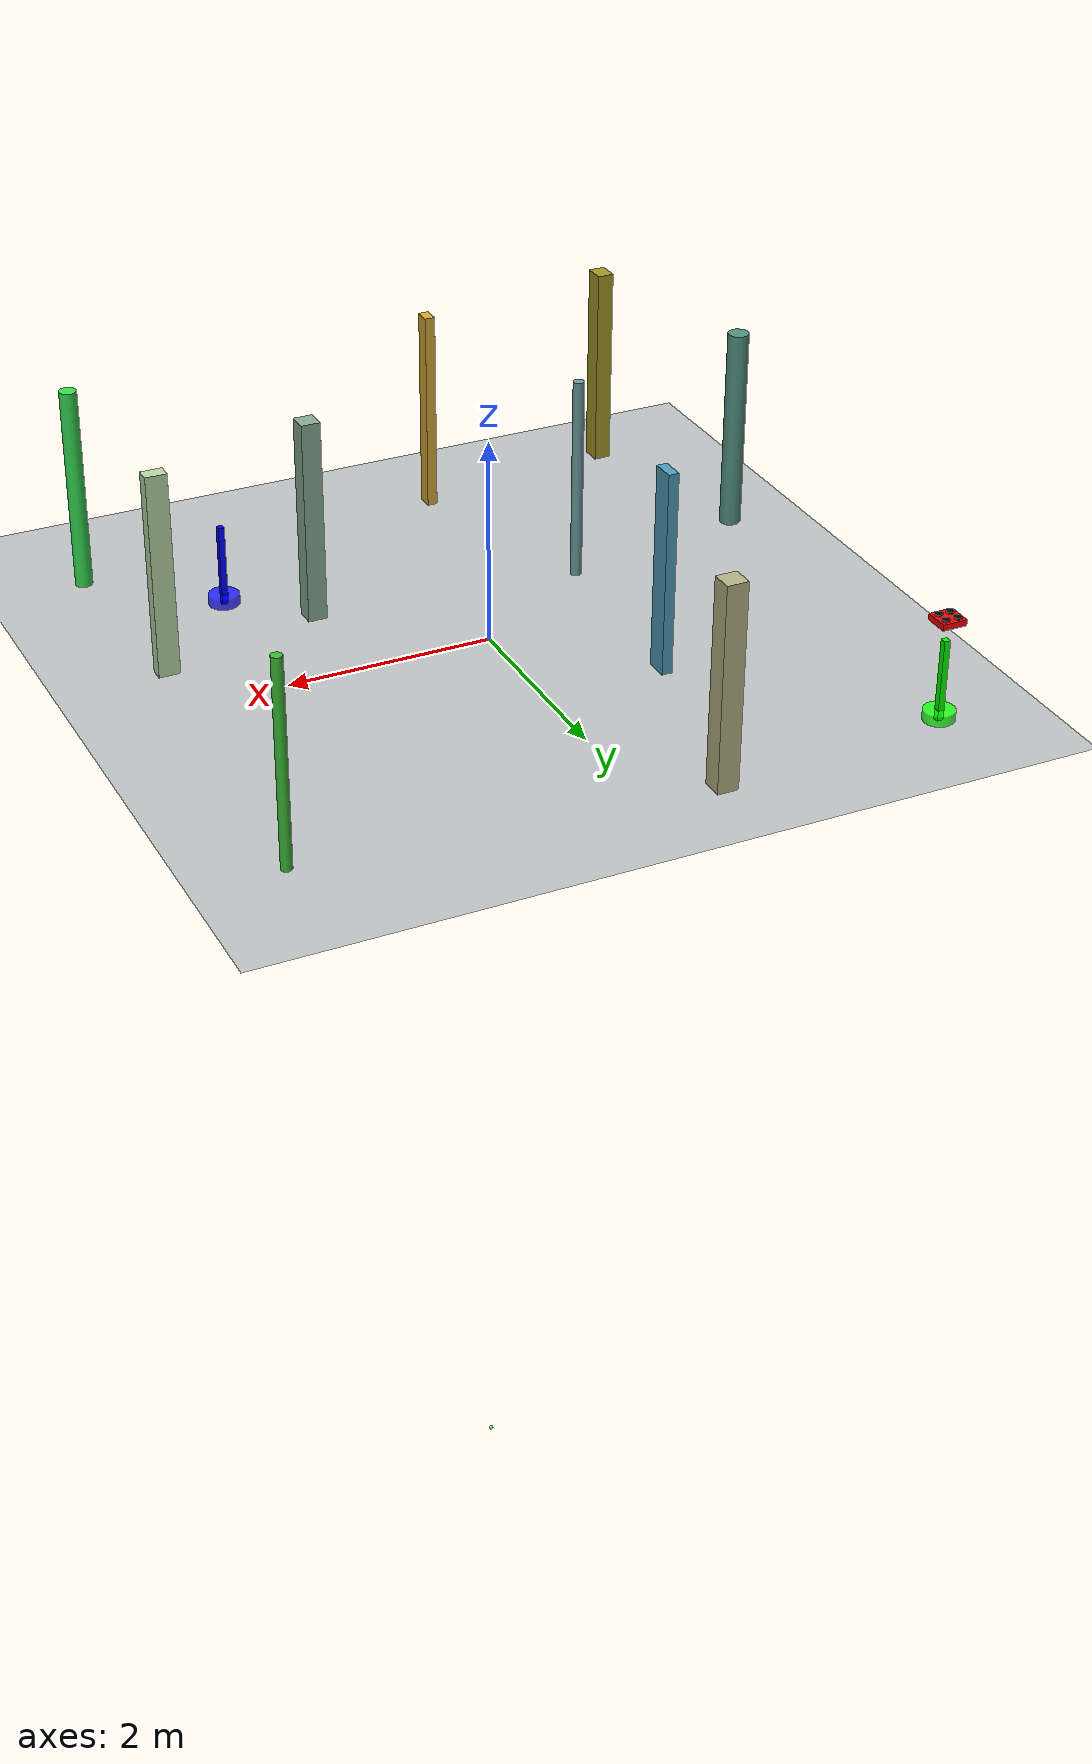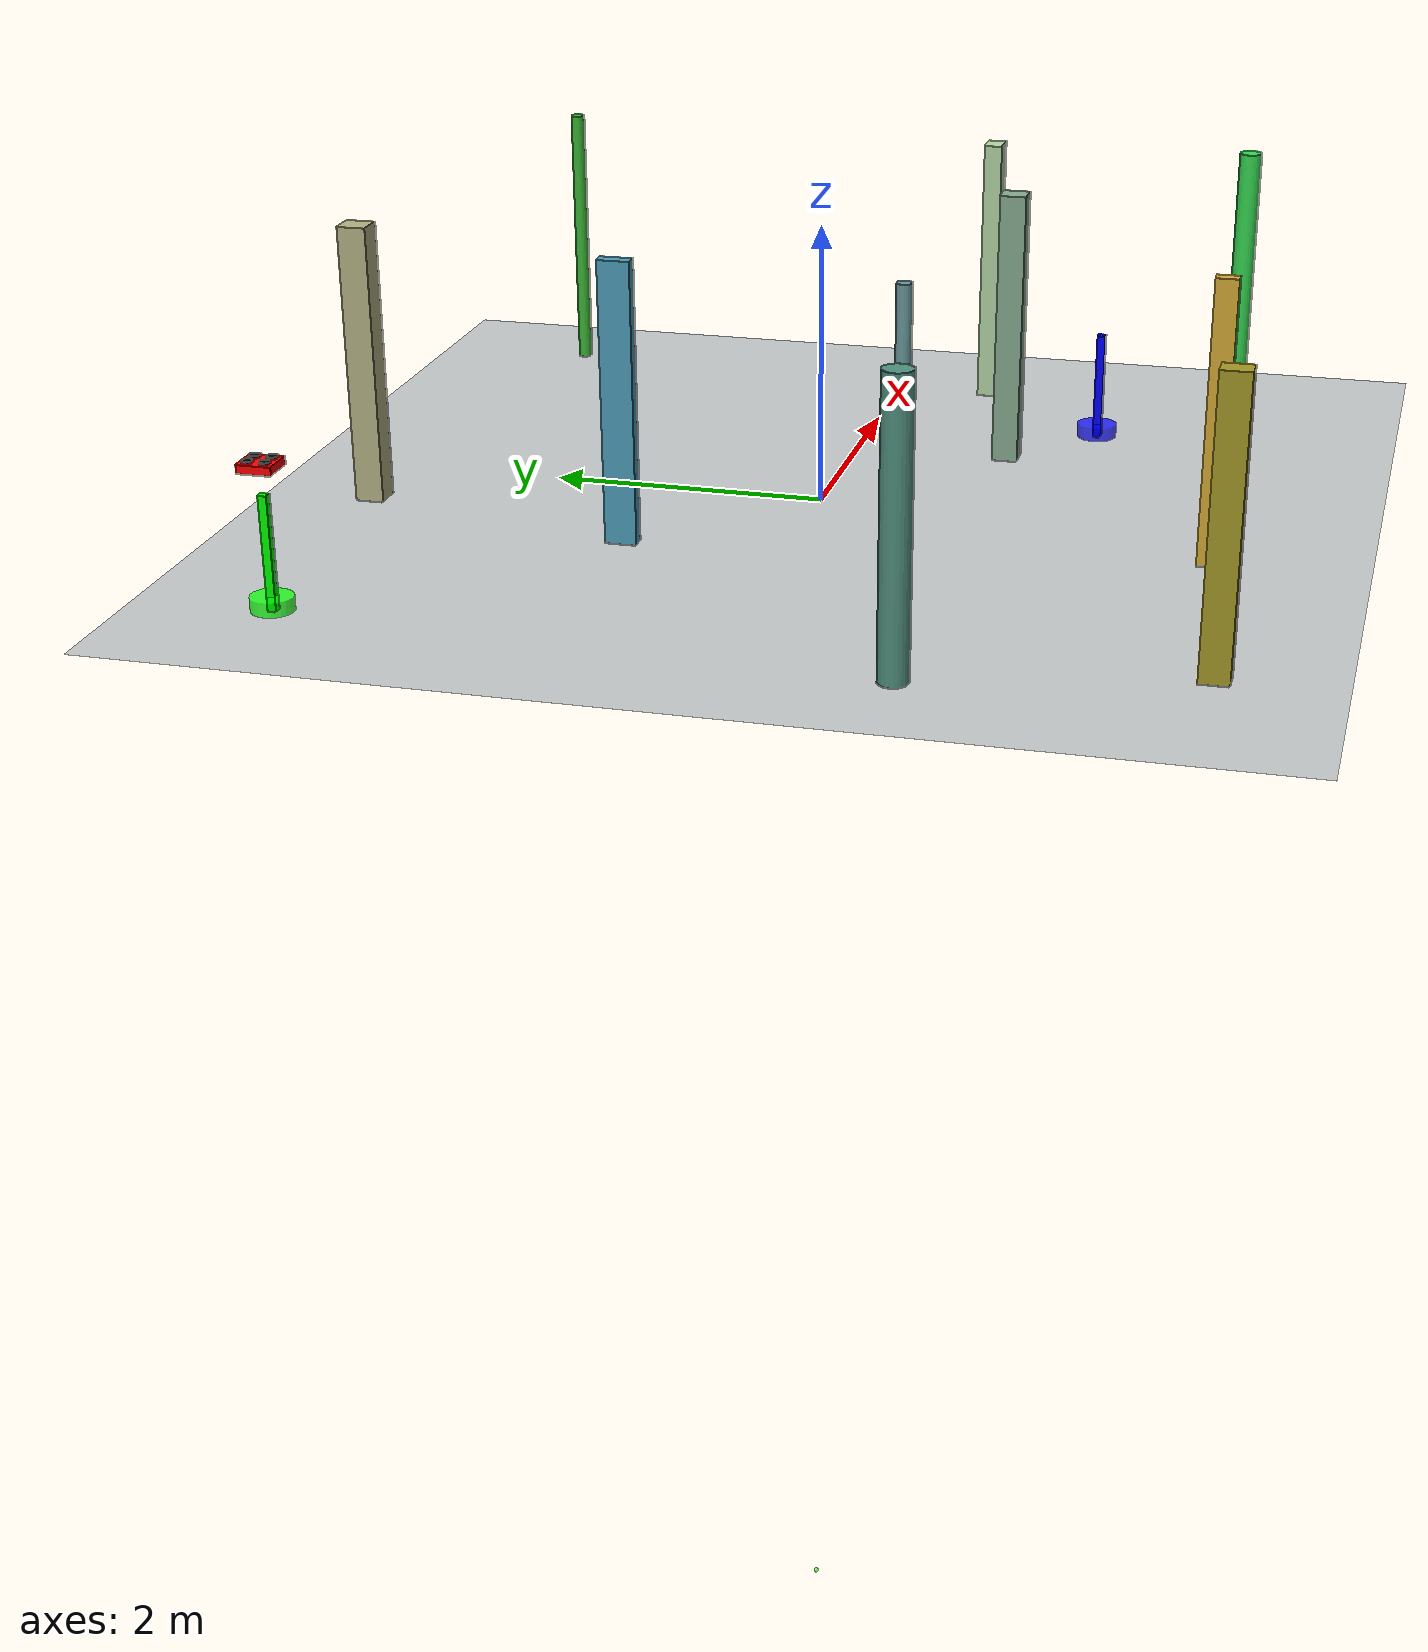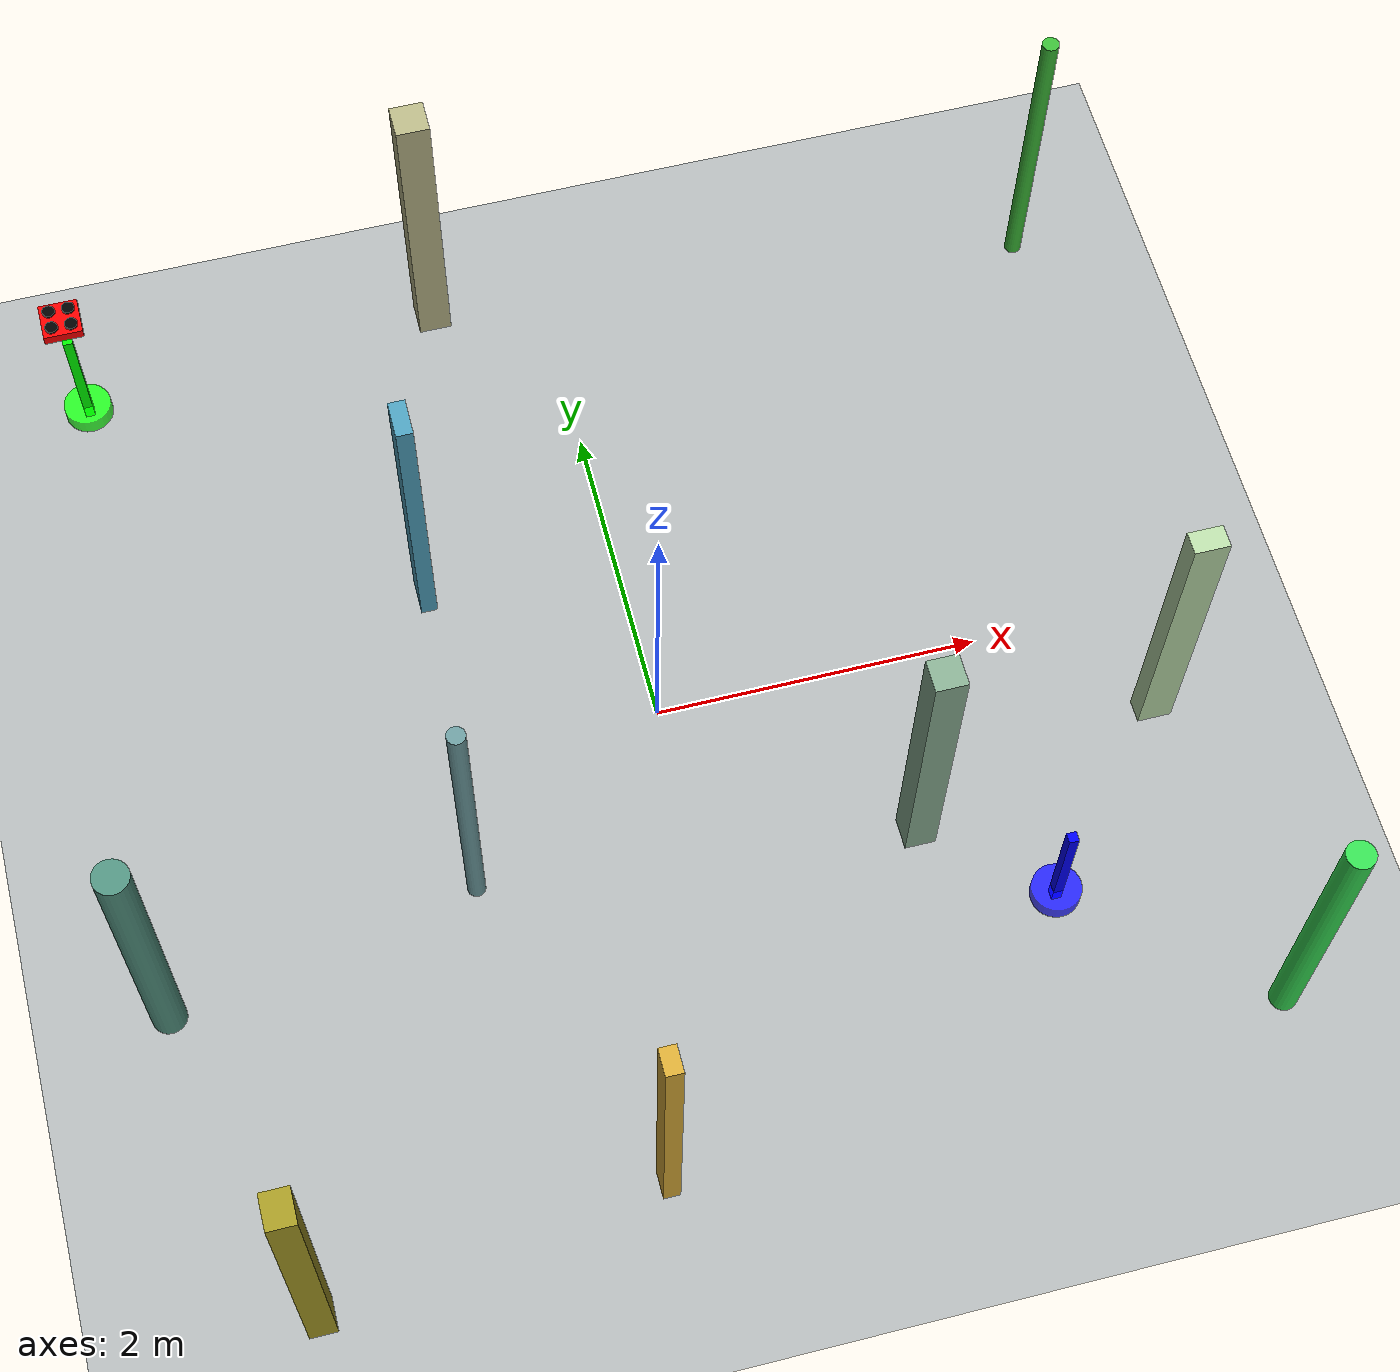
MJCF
<mujoco model="complex_uav_env">
  <compiler angle="degree" coordinate="local" inertiafromgeom="true"/>
  <option integrator="RK4" timestep="0.01"/>

  <visual>
    <headlight diffuse="0.6 0.6 0.6" ambient="0.3 0.3 0.3"/>
    <rgba haze="0.15 0.25 0.35 1"/>
    <global offwidth="2560" offheight="1440"/>
  </visual>

  <asset>
    <texture type="skybox" builtin="gradient" rgb1="0.3 0.5 0.7" rgb2="0 0 0" width="512" height="3072"/>
    <texture name="grid" type="2d" builtin="checker" rgb1="0.1 0.2 0.3" rgb2="0.2 0.3 0.4" width="512" height="512"/>
    <material name="grid" texture="grid" texrepeat="1 1" reflectance="0.2"/>
  </asset>

  <worldbody>
    <!-- Ground plane -->
    <geom name="ground" type="plane" size="4.0 4.0 0.1" material="grid"/>
    <light name="light1" pos="0 0 4" dir="0 0 -1" diffuse="1 1 1"/>

    <!-- Start position marker (green) -->
    <geom name="start_marker" type="cylinder" size="0.15 0.05" pos="-3.0 3.0 0.05" rgba="0 1 0 0.8"/>
    <geom name="start_pole" type="box" size="0.03 0.03 0.4" pos="-3.0 3.0 0.4" rgba="0 1 0 1"/>

    <!-- Goal position marker (blue) -->
    <geom name="goal_marker" type="cylinder" size="0.15 0.05" pos="1.9690485646893752 -1.7337336043769753 0.05" rgba="0 0 1 0.8"/>
    <geom name="goal_pole" type="box" size="0.03 0.03 0.4" pos="1.9690485646893752 -1.7337336043769753 0.4" rgba="0 0 1 1"/>

    <!-- UAV starting position -->
    <body name="chassis" pos="-3.0 3.0 1.0">
      <joint type="free" name="root"/>
      <geom name="uav_body" type="box" size="0.12 0.12 0.03" rgba="1.0 0.0 0.0 1.0" mass="0.8"/>

      <!-- Propeller arms and motors -->
      <geom type="box" size="0.06 0.008 0.004" pos="0 0 0.008" rgba="0.3 0.3 0.3 1"/>
      <geom type="box" size="0.008 0.06 0.004" pos="0 0 0.008" rgba="0.3 0.3 0.3 1"/>

      <!-- Motor visual geometry -->
      <geom type="cylinder" size="0.012 0.015" pos="0.06 0.06 0.012" rgba="0.2 0.2 0.2 1"/>
      <geom type="cylinder" size="0.012 0.015" pos="-0.06 0.06 0.012" rgba="0.2 0.2 0.2 1"/>
      <geom type="cylinder" size="0.012 0.015" pos="0.06 -0.06 0.012" rgba="0.2 0.2 0.2 1"/>
      <geom type="cylinder" size="0.012 0.015" pos="-0.06 -0.06 0.012" rgba="0.2 0.2 0.2 1"/>

      <!-- Propellers -->
      <geom name="prop1" type="cylinder" size="0.04 0.008" pos="0.06 0.06 0.04" rgba="0.0 0.0 0.0 1.0"/>
      <geom name="prop2" type="cylinder" size="0.04 0.008" pos="-0.06 0.06 0.04" rgba="0.0 0.0 0.0 1.0"/>
      <geom name="prop3" type="cylinder" size="0.04 0.008" pos="0.06 -0.06 0.04" rgba="0.0 0.0 0.0 1.0"/>
      <geom name="prop4" type="cylinder" size="0.04 0.008" pos="-0.06 -0.06 0.04" rgba="0.0 0.0 0.0 1.0"/>

      <!-- Sites for motor force application -->
      <site name="motor1" pos="0.06 0.06 0" size="0.01"/>
      <site name="motor2" pos="-0.06 0.06 0" size="0.01"/>
      <site name="motor3" pos="0.06 -0.06 0" size="0.01"/>
      <site name="motor4" pos="-0.06 -0.06 0" size="0.01"/>

      <!-- Depth camera sensor -->
      <camera name="uav_depth_camera" pos="0.15 0 0" xyaxes="0 1 0 0 0 1" fovy="90" mode="fixed"/>
    </body>
    <geom name="test_obs_0" type="box" size="0.10275140563555586 0.10367096505668662 1.0" pos="-0.7097543256119696 3.1878070844783855 1.0" rgba="0.7059191631181992 0.69783524132448 0.5172081698051094 1.0"/>
    <geom name="test_obs_1" type="cylinder" size="0.10370250312978697 1.0" pos="-3.2143093689901945 -1.2195264977549791 1.0" rgba="0.31288702705058746 0.5628104012482116 0.49252322683862915 1.0"/>
    <geom name="test_obs_2" type="cylinder" size="0.0838174777543088 1.0" pos="3.048764200415991 -2.676288535814264 1.0" rgba="0.20498939015464687 0.8535813852201041 0.31921830840290677 1.0"/>
    <geom name="test_obs_3" type="box" size="0.05089118066695251 0.1142332221088641 1.0" pos="-1.195001634236088 1.1475519312603586 1.0" rgba="0.2968173727158995 0.6156956817994452 0.724373909433008 1.0"/>
    <geom name="test_obs_4" type="box" size="0.08211143580825217 0.10217205227746455 1.0" pos="-2.7144314852355467 -3.157381470275228 1.0" rgba="0.6380628696753124 0.5928935753475816 0.1423593583359491 1.0"/>
    <geom name="test_obs_5" type="cylinder" size="0.05229042711081808 1.0" pos="3.137604624286633 2.794422222999353 1.0" rgba="0.23271444625220977 0.7272049305953676 0.21439666137954438 1.0"/>
    <geom name="test_obs_6" type="box" size="0.10446351154325534 0.0677400350723863 1.0" pos="2.913905871126496 -0.7014886834859818 1.0" rgba="0.7125269946593508 0.8426515560284633 0.6477258871184886 1.0"/>
    <geom name="test_obs_7" type="cylinder" size="0.05466643709166757 1.0" pos="-1.3219067970124434 -0.861857796385622 1.0" rgba="0.41536713013652826 0.5975790967414711 0.6114144583000845 1.0"/>
    <geom name="test_obs_8" type="box" size="0.05004295214417736 0.07948165833871577 1.0" pos="-0.6746921648222489 -2.888933562965215 1.0" rgba="0.8375044342527 0.6632115284156023 0.21026134638037652 1.0"/>
    <geom name="test_obs_9" type="box" size="0.09404739538423812 0.09610371209863766 1.0" pos="1.2924709573956474 -1.1383941576799108 1.0" rgba="0.525519776931132 0.6675778226789646 0.5634251508443515 1.0"/>
    <geom name="trail_0" type="sphere" size="0.02" pos="0 0 -10" rgba="0 1 0 0.6" contype="0" conaffinity="0"/>
    <geom name="trail_1" type="sphere" size="0.02" pos="0 0 -10" rgba="0 1 0 0.6" contype="0" conaffinity="0"/>
    <geom name="trail_2" type="sphere" size="0.02" pos="0 0 -10" rgba="0 1 0 0.6" contype="0" conaffinity="0"/>
    <geom name="trail_3" type="sphere" size="0.02" pos="0 0 -10" rgba="0 1 0 0.6" contype="0" conaffinity="0"/>
    <geom name="trail_4" type="sphere" size="0.02" pos="0 0 -10" rgba="0 1 0 0.6" contype="0" conaffinity="0"/>
    <geom name="trail_5" type="sphere" size="0.02" pos="0 0 -10" rgba="0 1 0 0.6" contype="0" conaffinity="0"/>
    <geom name="trail_6" type="sphere" size="0.02" pos="0 0 -10" rgba="0 1 0 0.6" contype="0" conaffinity="0"/>
    <geom name="trail_7" type="sphere" size="0.02" pos="0 0 -10" rgba="0 1 0 0.6" contype="0" conaffinity="0"/>
    <geom name="trail_8" type="sphere" size="0.02" pos="0 0 -10" rgba="0 1 0 0.6" contype="0" conaffinity="0"/>
    <geom name="trail_9" type="sphere" size="0.02" pos="0 0 -10" rgba="0 1 0 0.6" contype="0" conaffinity="0"/>
    <geom name="trail_10" type="sphere" size="0.02" pos="0 0 -10" rgba="0 1 0 0.6" contype="0" conaffinity="0"/>
    <geom name="trail_11" type="sphere" size="0.02" pos="0 0 -10" rgba="0 1 0 0.6" contype="0" conaffinity="0"/>
    <geom name="trail_12" type="sphere" size="0.02" pos="0 0 -10" rgba="0 1 0 0.6" contype="0" conaffinity="0"/>
    <geom name="trail_13" type="sphere" size="0.02" pos="0 0 -10" rgba="0 1 0 0.6" contype="0" conaffinity="0"/>
    <geom name="trail_14" type="sphere" size="0.02" pos="0 0 -10" rgba="0 1 0 0.6" contype="0" conaffinity="0"/>
    <geom name="trail_15" type="sphere" size="0.02" pos="0 0 -10" rgba="0 1 0 0.6" contype="0" conaffinity="0"/>
    <geom name="trail_16" type="sphere" size="0.02" pos="0 0 -10" rgba="0 1 0 0.6" contype="0" conaffinity="0"/>
    <geom name="trail_17" type="sphere" size="0.02" pos="0 0 -10" rgba="0 1 0 0.6" contype="0" conaffinity="0"/>
    <geom name="trail_18" type="sphere" size="0.02" pos="0 0 -10" rgba="0 1 0 0.6" contype="0" conaffinity="0"/>
    <geom name="trail_19" type="sphere" size="0.02" pos="0 0 -10" rgba="0 1 0 0.6" contype="0" conaffinity="0"/>
    <geom name="trail_20" type="sphere" size="0.02" pos="0 0 -10" rgba="0 1 0 0.6" contype="0" conaffinity="0"/>
    <geom name="trail_21" type="sphere" size="0.02" pos="0 0 -10" rgba="0 1 0 0.6" contype="0" conaffinity="0"/>
    <geom name="trail_22" type="sphere" size="0.02" pos="0 0 -10" rgba="0 1 0 0.6" contype="0" conaffinity="0"/>
    <geom name="trail_23" type="sphere" size="0.02" pos="0 0 -10" rgba="0 1 0 0.6" contype="0" conaffinity="0"/>
    <geom name="trail_24" type="sphere" size="0.02" pos="0 0 -10" rgba="0 1 0 0.6" contype="0" conaffinity="0"/>
    <geom name="trail_25" type="sphere" size="0.02" pos="0 0 -10" rgba="0 1 0 0.6" contype="0" conaffinity="0"/>
    <geom name="trail_26" type="sphere" size="0.02" pos="0 0 -10" rgba="0 1 0 0.6" contype="0" conaffinity="0"/>
    <geom name="trail_27" type="sphere" size="0.02" pos="0 0 -10" rgba="0 1 0 0.6" contype="0" conaffinity="0"/>
    <geom name="trail_28" type="sphere" size="0.02" pos="0 0 -10" rgba="0 1 0 0.6" contype="0" conaffinity="0"/>
    <geom name="trail_29" type="sphere" size="0.02" pos="0 0 -10" rgba="0 1 0 0.6" contype="0" conaffinity="0"/>
    <geom name="trail_30" type="sphere" size="0.02" pos="0 0 -10" rgba="0 1 0 0.6" contype="0" conaffinity="0"/>
    <geom name="trail_31" type="sphere" size="0.02" pos="0 0 -10" rgba="0 1 0 0.6" contype="0" conaffinity="0"/>
    <geom name="trail_32" type="sphere" size="0.02" pos="0 0 -10" rgba="0 1 0 0.6" contype="0" conaffinity="0"/>
    <geom name="trail_33" type="sphere" size="0.02" pos="0 0 -10" rgba="0 1 0 0.6" contype="0" conaffinity="0"/>
    <geom name="trail_34" type="sphere" size="0.02" pos="0 0 -10" rgba="0 1 0 0.6" contype="0" conaffinity="0"/>
    <geom name="trail_35" type="sphere" size="0.02" pos="0 0 -10" rgba="0 1 0 0.6" contype="0" conaffinity="0"/>
    <geom name="trail_36" type="sphere" size="0.02" pos="0 0 -10" rgba="0 1 0 0.6" contype="0" conaffinity="0"/>
    <geom name="trail_37" type="sphere" size="0.02" pos="0 0 -10" rgba="0 1 0 0.6" contype="0" conaffinity="0"/>
    <geom name="trail_38" type="sphere" size="0.02" pos="0 0 -10" rgba="0 1 0 0.6" contype="0" conaffinity="0"/>
    <geom name="trail_39" type="sphere" size="0.02" pos="0 0 -10" rgba="0 1 0 0.6" contype="0" conaffinity="0"/>
    <geom name="trail_40" type="sphere" size="0.02" pos="0 0 -10" rgba="0 1 0 0.6" contype="0" conaffinity="0"/>
    <geom name="trail_41" type="sphere" size="0.02" pos="0 0 -10" rgba="0 1 0 0.6" contype="0" conaffinity="0"/>
    <geom name="trail_42" type="sphere" size="0.02" pos="0 0 -10" rgba="0 1 0 0.6" contype="0" conaffinity="0"/>
    <geom name="trail_43" type="sphere" size="0.02" pos="0 0 -10" rgba="0 1 0 0.6" contype="0" conaffinity="0"/>
    <geom name="trail_44" type="sphere" size="0.02" pos="0 0 -10" rgba="0 1 0 0.6" contype="0" conaffinity="0"/>
    <geom name="trail_45" type="sphere" size="0.02" pos="0 0 -10" rgba="0 1 0 0.6" contype="0" conaffinity="0"/>
    <geom name="trail_46" type="sphere" size="0.02" pos="0 0 -10" rgba="0 1 0 0.6" contype="0" conaffinity="0"/>
    <geom name="trail_47" type="sphere" size="0.02" pos="0 0 -10" rgba="0 1 0 0.6" contype="0" conaffinity="0"/>
    <geom name="trail_48" type="sphere" size="0.02" pos="0 0 -10" rgba="0 1 0 0.6" contype="0" conaffinity="0"/>
    <geom name="trail_49" type="sphere" size="0.02" pos="0 0 -10" rgba="0 1 0 0.6" contype="0" conaffinity="0"/>
    <geom name="trail_50" type="sphere" size="0.02" pos="0 0 -10" rgba="0 1 0 0.6" contype="0" conaffinity="0"/>
    <geom name="trail_51" type="sphere" size="0.02" pos="0 0 -10" rgba="0 1 0 0.6" contype="0" conaffinity="0"/>
    <geom name="trail_52" type="sphere" size="0.02" pos="0 0 -10" rgba="0 1 0 0.6" contype="0" conaffinity="0"/>
    <geom name="trail_53" type="sphere" size="0.02" pos="0 0 -10" rgba="0 1 0 0.6" contype="0" conaffinity="0"/>
    <geom name="trail_54" type="sphere" size="0.02" pos="0 0 -10" rgba="0 1 0 0.6" contype="0" conaffinity="0"/>
    <geom name="trail_55" type="sphere" size="0.02" pos="0 0 -10" rgba="0 1 0 0.6" contype="0" conaffinity="0"/>
    <geom name="trail_56" type="sphere" size="0.02" pos="0 0 -10" rgba="0 1 0 0.6" contype="0" conaffinity="0"/>
    <geom name="trail_57" type="sphere" size="0.02" pos="0 0 -10" rgba="0 1 0 0.6" contype="0" conaffinity="0"/>
    <geom name="trail_58" type="sphere" size="0.02" pos="0 0 -10" rgba="0 1 0 0.6" contype="0" conaffinity="0"/>
    <geom name="trail_59" type="sphere" size="0.02" pos="0 0 -10" rgba="0 1 0 0.6" contype="0" conaffinity="0"/>
    <geom name="trail_60" type="sphere" size="0.02" pos="0 0 -10" rgba="0 1 0 0.6" contype="0" conaffinity="0"/>
    <geom name="trail_61" type="sphere" size="0.02" pos="0 0 -10" rgba="0 1 0 0.6" contype="0" conaffinity="0"/>
    <geom name="trail_62" type="sphere" size="0.02" pos="0 0 -10" rgba="0 1 0 0.6" contype="0" conaffinity="0"/>
    <geom name="trail_63" type="sphere" size="0.02" pos="0 0 -10" rgba="0 1 0 0.6" contype="0" conaffinity="0"/>
    <geom name="trail_64" type="sphere" size="0.02" pos="0 0 -10" rgba="0 1 0 0.6" contype="0" conaffinity="0"/>
    <geom name="trail_65" type="sphere" size="0.02" pos="0 0 -10" rgba="0 1 0 0.6" contype="0" conaffinity="0"/>
    <geom name="trail_66" type="sphere" size="0.02" pos="0 0 -10" rgba="0 1 0 0.6" contype="0" conaffinity="0"/>
    <geom name="trail_67" type="sphere" size="0.02" pos="0 0 -10" rgba="0 1 0 0.6" contype="0" conaffinity="0"/>
    <geom name="trail_68" type="sphere" size="0.02" pos="0 0 -10" rgba="0 1 0 0.6" contype="0" conaffinity="0"/>
    <geom name="trail_69" type="sphere" size="0.02" pos="0 0 -10" rgba="0 1 0 0.6" contype="0" conaffinity="0"/>
    <geom name="trail_70" type="sphere" size="0.02" pos="0 0 -10" rgba="0 1 0 0.6" contype="0" conaffinity="0"/>
    <geom name="trail_71" type="sphere" size="0.02" pos="0 0 -10" rgba="0 1 0 0.6" contype="0" conaffinity="0"/>
    <geom name="trail_72" type="sphere" size="0.02" pos="0 0 -10" rgba="0 1 0 0.6" contype="0" conaffinity="0"/>
    <geom name="trail_73" type="sphere" size="0.02" pos="0 0 -10" rgba="0 1 0 0.6" contype="0" conaffinity="0"/>
    <geom name="trail_74" type="sphere" size="0.02" pos="0 0 -10" rgba="0 1 0 0.6" contype="0" conaffinity="0"/>
    <geom name="trail_75" type="sphere" size="0.02" pos="0 0 -10" rgba="0 1 0 0.6" contype="0" conaffinity="0"/>
    <geom name="trail_76" type="sphere" size="0.02" pos="0 0 -10" rgba="0 1 0 0.6" contype="0" conaffinity="0"/>
    <geom name="trail_77" type="sphere" size="0.02" pos="0 0 -10" rgba="0 1 0 0.6" contype="0" conaffinity="0"/>
    <geom name="trail_78" type="sphere" size="0.02" pos="0 0 -10" rgba="0 1 0 0.6" contype="0" conaffinity="0"/>
    <geom name="trail_79" type="sphere" size="0.02" pos="0 0 -10" rgba="0 1 0 0.6" contype="0" conaffinity="0"/>
    <geom name="trail_80" type="sphere" size="0.02" pos="0 0 -10" rgba="0 1 0 0.6" contype="0" conaffinity="0"/>
    <geom name="trail_81" type="sphere" size="0.02" pos="0 0 -10" rgba="0 1 0 0.6" contype="0" conaffinity="0"/>
    <geom name="trail_82" type="sphere" size="0.02" pos="0 0 -10" rgba="0 1 0 0.6" contype="0" conaffinity="0"/>
    <geom name="trail_83" type="sphere" size="0.02" pos="0 0 -10" rgba="0 1 0 0.6" contype="0" conaffinity="0"/>
    <geom name="trail_84" type="sphere" size="0.02" pos="0 0 -10" rgba="0 1 0 0.6" contype="0" conaffinity="0"/>
    <geom name="trail_85" type="sphere" size="0.02" pos="0 0 -10" rgba="0 1 0 0.6" contype="0" conaffinity="0"/>
    <geom name="trail_86" type="sphere" size="0.02" pos="0 0 -10" rgba="0 1 0 0.6" contype="0" conaffinity="0"/>
    <geom name="trail_87" type="sphere" size="0.02" pos="0 0 -10" rgba="0 1 0 0.6" contype="0" conaffinity="0"/>
    <geom name="trail_88" type="sphere" size="0.02" pos="0 0 -10" rgba="0 1 0 0.6" contype="0" conaffinity="0"/>
    <geom name="trail_89" type="sphere" size="0.02" pos="0 0 -10" rgba="0 1 0 0.6" contype="0" conaffinity="0"/>
    <geom name="trail_90" type="sphere" size="0.02" pos="0 0 -10" rgba="0 1 0 0.6" contype="0" conaffinity="0"/>
    <geom name="trail_91" type="sphere" size="0.02" pos="0 0 -10" rgba="0 1 0 0.6" contype="0" conaffinity="0"/>
    <geom name="trail_92" type="sphere" size="0.02" pos="0 0 -10" rgba="0 1 0 0.6" contype="0" conaffinity="0"/>
    <geom name="trail_93" type="sphere" size="0.02" pos="0 0 -10" rgba="0 1 0 0.6" contype="0" conaffinity="0"/>
    <geom name="trail_94" type="sphere" size="0.02" pos="0 0 -10" rgba="0 1 0 0.6" contype="0" conaffinity="0"/>
    <geom name="trail_95" type="sphere" size="0.02" pos="0 0 -10" rgba="0 1 0 0.6" contype="0" conaffinity="0"/>
    <geom name="trail_96" type="sphere" size="0.02" pos="0 0 -10" rgba="0 1 0 0.6" contype="0" conaffinity="0"/>
    <geom name="trail_97" type="sphere" size="0.02" pos="0 0 -10" rgba="0 1 0 0.6" contype="0" conaffinity="0"/>
    <geom name="trail_98" type="sphere" size="0.02" pos="0 0 -10" rgba="0 1 0 0.6" contype="0" conaffinity="0"/>
    <geom name="trail_99" type="sphere" size="0.02" pos="0 0 -10" rgba="0 1 0 0.6" contype="0" conaffinity="0"/>
    <geom name="trail_100" type="sphere" size="0.02" pos="0 0 -10" rgba="0 1 0 0.6" contype="0" conaffinity="0"/>
    <geom name="trail_101" type="sphere" size="0.02" pos="0 0 -10" rgba="0 1 0 0.6" contype="0" conaffinity="0"/>
    <geom name="trail_102" type="sphere" size="0.02" pos="0 0 -10" rgba="0 1 0 0.6" contype="0" conaffinity="0"/>
    <geom name="trail_103" type="sphere" size="0.02" pos="0 0 -10" rgba="0 1 0 0.6" contype="0" conaffinity="0"/>
    <geom name="trail_104" type="sphere" size="0.02" pos="0 0 -10" rgba="0 1 0 0.6" contype="0" conaffinity="0"/>
    <geom name="trail_105" type="sphere" size="0.02" pos="0 0 -10" rgba="0 1 0 0.6" contype="0" conaffinity="0"/>
    <geom name="trail_106" type="sphere" size="0.02" pos="0 0 -10" rgba="0 1 0 0.6" contype="0" conaffinity="0"/>
    <geom name="trail_107" type="sphere" size="0.02" pos="0 0 -10" rgba="0 1 0 0.6" contype="0" conaffinity="0"/>
    <geom name="trail_108" type="sphere" size="0.02" pos="0 0 -10" rgba="0 1 0 0.6" contype="0" conaffinity="0"/>
    <geom name="trail_109" type="sphere" size="0.02" pos="0 0 -10" rgba="0 1 0 0.6" contype="0" conaffinity="0"/>
    <geom name="trail_110" type="sphere" size="0.02" pos="0 0 -10" rgba="0 1 0 0.6" contype="0" conaffinity="0"/>
    <geom name="trail_111" type="sphere" size="0.02" pos="0 0 -10" rgba="0 1 0 0.6" contype="0" conaffinity="0"/>
    <geom name="trail_112" type="sphere" size="0.02" pos="0 0 -10" rgba="0 1 0 0.6" contype="0" conaffinity="0"/>
    <geom name="trail_113" type="sphere" size="0.02" pos="0 0 -10" rgba="0 1 0 0.6" contype="0" conaffinity="0"/>
    <geom name="trail_114" type="sphere" size="0.02" pos="0 0 -10" rgba="0 1 0 0.6" contype="0" conaffinity="0"/>
    <geom name="trail_115" type="sphere" size="0.02" pos="0 0 -10" rgba="0 1 0 0.6" contype="0" conaffinity="0"/>
    <geom name="trail_116" type="sphere" size="0.02" pos="0 0 -10" rgba="0 1 0 0.6" contype="0" conaffinity="0"/>
    <geom name="trail_117" type="sphere" size="0.02" pos="0 0 -10" rgba="0 1 0 0.6" contype="0" conaffinity="0"/>
    <geom name="trail_118" type="sphere" size="0.02" pos="0 0 -10" rgba="0 1 0 0.6" contype="0" conaffinity="0"/>
    <geom name="trail_119" type="sphere" size="0.02" pos="0 0 -10" rgba="0 1 0 0.6" contype="0" conaffinity="0"/>
    <geom name="trail_120" type="sphere" size="0.02" pos="0 0 -10" rgba="0 1 0 0.6" contype="0" conaffinity="0"/>
    <geom name="trail_121" type="sphere" size="0.02" pos="0 0 -10" rgba="0 1 0 0.6" contype="0" conaffinity="0"/>
    <geom name="trail_122" type="sphere" size="0.02" pos="0 0 -10" rgba="0 1 0 0.6" contype="0" conaffinity="0"/>
    <geom name="trail_123" type="sphere" size="0.02" pos="0 0 -10" rgba="0 1 0 0.6" contype="0" conaffinity="0"/>
    <geom name="trail_124" type="sphere" size="0.02" pos="0 0 -10" rgba="0 1 0 0.6" contype="0" conaffinity="0"/>
    <geom name="trail_125" type="sphere" size="0.02" pos="0 0 -10" rgba="0 1 0 0.6" contype="0" conaffinity="0"/>
    <geom name="trail_126" type="sphere" size="0.02" pos="0 0 -10" rgba="0 1 0 0.6" contype="0" conaffinity="0"/>
    <geom name="trail_127" type="sphere" size="0.02" pos="0 0 -10" rgba="0 1 0 0.6" contype="0" conaffinity="0"/>
    <geom name="trail_128" type="sphere" size="0.02" pos="0 0 -10" rgba="0 1 0 0.6" contype="0" conaffinity="0"/>
    <geom name="trail_129" type="sphere" size="0.02" pos="0 0 -10" rgba="0 1 0 0.6" contype="0" conaffinity="0"/>
    <geom name="trail_130" type="sphere" size="0.02" pos="0 0 -10" rgba="0 1 0 0.6" contype="0" conaffinity="0"/>
    <geom name="trail_131" type="sphere" size="0.02" pos="0 0 -10" rgba="0 1 0 0.6" contype="0" conaffinity="0"/>
    <geom name="trail_132" type="sphere" size="0.02" pos="0 0 -10" rgba="0 1 0 0.6" contype="0" conaffinity="0"/>
    <geom name="trail_133" type="sphere" size="0.02" pos="0 0 -10" rgba="0 1 0 0.6" contype="0" conaffinity="0"/>
    <geom name="trail_134" type="sphere" size="0.02" pos="0 0 -10" rgba="0 1 0 0.6" contype="0" conaffinity="0"/>
    <geom name="trail_135" type="sphere" size="0.02" pos="0 0 -10" rgba="0 1 0 0.6" contype="0" conaffinity="0"/>
    <geom name="trail_136" type="sphere" size="0.02" pos="0 0 -10" rgba="0 1 0 0.6" contype="0" conaffinity="0"/>
    <geom name="trail_137" type="sphere" size="0.02" pos="0 0 -10" rgba="0 1 0 0.6" contype="0" conaffinity="0"/>
    <geom name="trail_138" type="sphere" size="0.02" pos="0 0 -10" rgba="0 1 0 0.6" contype="0" conaffinity="0"/>
    <geom name="trail_139" type="sphere" size="0.02" pos="0 0 -10" rgba="0 1 0 0.6" contype="0" conaffinity="0"/>
    <geom name="trail_140" type="sphere" size="0.02" pos="0 0 -10" rgba="0 1 0 0.6" contype="0" conaffinity="0"/>
    <geom name="trail_141" type="sphere" size="0.02" pos="0 0 -10" rgba="0 1 0 0.6" contype="0" conaffinity="0"/>
    <geom name="trail_142" type="sphere" size="0.02" pos="0 0 -10" rgba="0 1 0 0.6" contype="0" conaffinity="0"/>
    <geom name="trail_143" type="sphere" size="0.02" pos="0 0 -10" rgba="0 1 0 0.6" contype="0" conaffinity="0"/>
    <geom name="trail_144" type="sphere" size="0.02" pos="0 0 -10" rgba="0 1 0 0.6" contype="0" conaffinity="0"/>
    <geom name="trail_145" type="sphere" size="0.02" pos="0 0 -10" rgba="0 1 0 0.6" contype="0" conaffinity="0"/>
    <geom name="trail_146" type="sphere" size="0.02" pos="0 0 -10" rgba="0 1 0 0.6" contype="0" conaffinity="0"/>
    <geom name="trail_147" type="sphere" size="0.02" pos="0 0 -10" rgba="0 1 0 0.6" contype="0" conaffinity="0"/>
    <geom name="trail_148" type="sphere" size="0.02" pos="0 0 -10" rgba="0 1 0 0.6" contype="0" conaffinity="0"/>
    <geom name="trail_149" type="sphere" size="0.02" pos="0 0 -10" rgba="0 1 0 0.6" contype="0" conaffinity="0"/>
    <geom name="trail_150" type="sphere" size="0.02" pos="0 0 -10" rgba="0 1 0 0.6" contype="0" conaffinity="0"/>
    <geom name="trail_151" type="sphere" size="0.02" pos="0 0 -10" rgba="0 1 0 0.6" contype="0" conaffinity="0"/>
    <geom name="trail_152" type="sphere" size="0.02" pos="0 0 -10" rgba="0 1 0 0.6" contype="0" conaffinity="0"/>
    <geom name="trail_153" type="sphere" size="0.02" pos="0 0 -10" rgba="0 1 0 0.6" contype="0" conaffinity="0"/>
    <geom name="trail_154" type="sphere" size="0.02" pos="0 0 -10" rgba="0 1 0 0.6" contype="0" conaffinity="0"/>
    <geom name="trail_155" type="sphere" size="0.02" pos="0 0 -10" rgba="0 1 0 0.6" contype="0" conaffinity="0"/>
    <geom name="trail_156" type="sphere" size="0.02" pos="0 0 -10" rgba="0 1 0 0.6" contype="0" conaffinity="0"/>
    <geom name="trail_157" type="sphere" size="0.02" pos="0 0 -10" rgba="0 1 0 0.6" contype="0" conaffinity="0"/>
    <geom name="trail_158" type="sphere" size="0.02" pos="0 0 -10" rgba="0 1 0 0.6" contype="0" conaffinity="0"/>
    <geom name="trail_159" type="sphere" size="0.02" pos="0 0 -10" rgba="0 1 0 0.6" contype="0" conaffinity="0"/>
    <geom name="trail_160" type="sphere" size="0.02" pos="0 0 -10" rgba="0 1 0 0.6" contype="0" conaffinity="0"/>
    <geom name="trail_161" type="sphere" size="0.02" pos="0 0 -10" rgba="0 1 0 0.6" contype="0" conaffinity="0"/>
    <geom name="trail_162" type="sphere" size="0.02" pos="0 0 -10" rgba="0 1 0 0.6" contype="0" conaffinity="0"/>
    <geom name="trail_163" type="sphere" size="0.02" pos="0 0 -10" rgba="0 1 0 0.6" contype="0" conaffinity="0"/>
    <geom name="trail_164" type="sphere" size="0.02" pos="0 0 -10" rgba="0 1 0 0.6" contype="0" conaffinity="0"/>
    <geom name="trail_165" type="sphere" size="0.02" pos="0 0 -10" rgba="0 1 0 0.6" contype="0" conaffinity="0"/>
    <geom name="trail_166" type="sphere" size="0.02" pos="0 0 -10" rgba="0 1 0 0.6" contype="0" conaffinity="0"/>
    <geom name="trail_167" type="sphere" size="0.02" pos="0 0 -10" rgba="0 1 0 0.6" contype="0" conaffinity="0"/>
    <geom name="trail_168" type="sphere" size="0.02" pos="0 0 -10" rgba="0 1 0 0.6" contype="0" conaffinity="0"/>
    <geom name="trail_169" type="sphere" size="0.02" pos="0 0 -10" rgba="0 1 0 0.6" contype="0" conaffinity="0"/>
    <geom name="trail_170" type="sphere" size="0.02" pos="0 0 -10" rgba="0 1 0 0.6" contype="0" conaffinity="0"/>
    <geom name="trail_171" type="sphere" size="0.02" pos="0 0 -10" rgba="0 1 0 0.6" contype="0" conaffinity="0"/>
    <geom name="trail_172" type="sphere" size="0.02" pos="0 0 -10" rgba="0 1 0 0.6" contype="0" conaffinity="0"/>
    <geom name="trail_173" type="sphere" size="0.02" pos="0 0 -10" rgba="0 1 0 0.6" contype="0" conaffinity="0"/>
    <geom name="trail_174" type="sphere" size="0.02" pos="0 0 -10" rgba="0 1 0 0.6" contype="0" conaffinity="0"/>
    <geom name="trail_175" type="sphere" size="0.02" pos="0 0 -10" rgba="0 1 0 0.6" contype="0" conaffinity="0"/>
    <geom name="trail_176" type="sphere" size="0.02" pos="0 0 -10" rgba="0 1 0 0.6" contype="0" conaffinity="0"/>
    <geom name="trail_177" type="sphere" size="0.02" pos="0 0 -10" rgba="0 1 0 0.6" contype="0" conaffinity="0"/>
    <geom name="trail_178" type="sphere" size="0.02" pos="0 0 -10" rgba="0 1 0 0.6" contype="0" conaffinity="0"/>
    <geom name="trail_179" type="sphere" size="0.02" pos="0 0 -10" rgba="0 1 0 0.6" contype="0" conaffinity="0"/>
    <geom name="trail_180" type="sphere" size="0.02" pos="0 0 -10" rgba="0 1 0 0.6" contype="0" conaffinity="0"/>
    <geom name="trail_181" type="sphere" size="0.02" pos="0 0 -10" rgba="0 1 0 0.6" contype="0" conaffinity="0"/>
    <geom name="trail_182" type="sphere" size="0.02" pos="0 0 -10" rgba="0 1 0 0.6" contype="0" conaffinity="0"/>
    <geom name="trail_183" type="sphere" size="0.02" pos="0 0 -10" rgba="0 1 0 0.6" contype="0" conaffinity="0"/>
    <geom name="trail_184" type="sphere" size="0.02" pos="0 0 -10" rgba="0 1 0 0.6" contype="0" conaffinity="0"/>
    <geom name="trail_185" type="sphere" size="0.02" pos="0 0 -10" rgba="0 1 0 0.6" contype="0" conaffinity="0"/>
    <geom name="trail_186" type="sphere" size="0.02" pos="0 0 -10" rgba="0 1 0 0.6" contype="0" conaffinity="0"/>
    <geom name="trail_187" type="sphere" size="0.02" pos="0 0 -10" rgba="0 1 0 0.6" contype="0" conaffinity="0"/>
    <geom name="trail_188" type="sphere" size="0.02" pos="0 0 -10" rgba="0 1 0 0.6" contype="0" conaffinity="0"/>
    <geom name="trail_189" type="sphere" size="0.02" pos="0 0 -10" rgba="0 1 0 0.6" contype="0" conaffinity="0"/>
    <geom name="trail_190" type="sphere" size="0.02" pos="0 0 -10" rgba="0 1 0 0.6" contype="0" conaffinity="0"/>
    <geom name="trail_191" type="sphere" size="0.02" pos="0 0 -10" rgba="0 1 0 0.6" contype="0" conaffinity="0"/>
    <geom name="trail_192" type="sphere" size="0.02" pos="0 0 -10" rgba="0 1 0 0.6" contype="0" conaffinity="0"/>
    <geom name="trail_193" type="sphere" size="0.02" pos="0 0 -10" rgba="0 1 0 0.6" contype="0" conaffinity="0"/>
    <geom name="trail_194" type="sphere" size="0.02" pos="0 0 -10" rgba="0 1 0 0.6" contype="0" conaffinity="0"/>
    <geom name="trail_195" type="sphere" size="0.02" pos="0 0 -10" rgba="0 1 0 0.6" contype="0" conaffinity="0"/>
    <geom name="trail_196" type="sphere" size="0.02" pos="0 0 -10" rgba="0 1 0 0.6" contype="0" conaffinity="0"/>
    <geom name="trail_197" type="sphere" size="0.02" pos="0 0 -10" rgba="0 1 0 0.6" contype="0" conaffinity="0"/>
    <geom name="trail_198" type="sphere" size="0.02" pos="0 0 -10" rgba="0 1 0 0.6" contype="0" conaffinity="0"/>
    <geom name="trail_199" type="sphere" size="0.02" pos="0 0 -10" rgba="0 1 0 0.6" contype="0" conaffinity="0"/>
    <geom name="trail_200" type="sphere" size="0.02" pos="0 0 -10" rgba="0 1 0 0.6" contype="0" conaffinity="0"/>
    <geom name="trail_201" type="sphere" size="0.02" pos="0 0 -10" rgba="0 1 0 0.6" contype="0" conaffinity="0"/>
    <geom name="trail_202" type="sphere" size="0.02" pos="0 0 -10" rgba="0 1 0 0.6" contype="0" conaffinity="0"/>
    <geom name="trail_203" type="sphere" size="0.02" pos="0 0 -10" rgba="0 1 0 0.6" contype="0" conaffinity="0"/>
    <geom name="trail_204" type="sphere" size="0.02" pos="0 0 -10" rgba="0 1 0 0.6" contype="0" conaffinity="0"/>
    <geom name="trail_205" type="sphere" size="0.02" pos="0 0 -10" rgba="0 1 0 0.6" contype="0" conaffinity="0"/>
    <geom name="trail_206" type="sphere" size="0.02" pos="0 0 -10" rgba="0 1 0 0.6" contype="0" conaffinity="0"/>
    <geom name="trail_207" type="sphere" size="0.02" pos="0 0 -10" rgba="0 1 0 0.6" contype="0" conaffinity="0"/>
    <geom name="trail_208" type="sphere" size="0.02" pos="0 0 -10" rgba="0 1 0 0.6" contype="0" conaffinity="0"/>
    <geom name="trail_209" type="sphere" size="0.02" pos="0 0 -10" rgba="0 1 0 0.6" contype="0" conaffinity="0"/>
    <geom name="trail_210" type="sphere" size="0.02" pos="0 0 -10" rgba="0 1 0 0.6" contype="0" conaffinity="0"/>
    <geom name="trail_211" type="sphere" size="0.02" pos="0 0 -10" rgba="0 1 0 0.6" contype="0" conaffinity="0"/>
    <geom name="trail_212" type="sphere" size="0.02" pos="0 0 -10" rgba="0 1 0 0.6" contype="0" conaffinity="0"/>
    <geom name="trail_213" type="sphere" size="0.02" pos="0 0 -10" rgba="0 1 0 0.6" contype="0" conaffinity="0"/>
    <geom name="trail_214" type="sphere" size="0.02" pos="0 0 -10" rgba="0 1 0 0.6" contype="0" conaffinity="0"/>
    <geom name="trail_215" type="sphere" size="0.02" pos="0 0 -10" rgba="0 1 0 0.6" contype="0" conaffinity="0"/>
    <geom name="trail_216" type="sphere" size="0.02" pos="0 0 -10" rgba="0 1 0 0.6" contype="0" conaffinity="0"/>
    <geom name="trail_217" type="sphere" size="0.02" pos="0 0 -10" rgba="0 1 0 0.6" contype="0" conaffinity="0"/>
    <geom name="trail_218" type="sphere" size="0.02" pos="0 0 -10" rgba="0 1 0 0.6" contype="0" conaffinity="0"/>
    <geom name="trail_219" type="sphere" size="0.02" pos="0 0 -10" rgba="0 1 0 0.6" contype="0" conaffinity="0"/>
    <geom name="trail_220" type="sphere" size="0.02" pos="0 0 -10" rgba="0 1 0 0.6" contype="0" conaffinity="0"/>
    <geom name="trail_221" type="sphere" size="0.02" pos="0 0 -10" rgba="0 1 0 0.6" contype="0" conaffinity="0"/>
    <geom name="trail_222" type="sphere" size="0.02" pos="0 0 -10" rgba="0 1 0 0.6" contype="0" conaffinity="0"/>
    <geom name="trail_223" type="sphere" size="0.02" pos="0 0 -10" rgba="0 1 0 0.6" contype="0" conaffinity="0"/>
    <geom name="trail_224" type="sphere" size="0.02" pos="0 0 -10" rgba="0 1 0 0.6" contype="0" conaffinity="0"/>
    <geom name="trail_225" type="sphere" size="0.02" pos="0 0 -10" rgba="0 1 0 0.6" contype="0" conaffinity="0"/>
    <geom name="trail_226" type="sphere" size="0.02" pos="0 0 -10" rgba="0 1 0 0.6" contype="0" conaffinity="0"/>
    <geom name="trail_227" type="sphere" size="0.02" pos="0 0 -10" rgba="0 1 0 0.6" contype="0" conaffinity="0"/>
    <geom name="trail_228" type="sphere" size="0.02" pos="0 0 -10" rgba="0 1 0 0.6" contype="0" conaffinity="0"/>
    <geom name="trail_229" type="sphere" size="0.02" pos="0 0 -10" rgba="0 1 0 0.6" contype="0" conaffinity="0"/>
    <geom name="trail_230" type="sphere" size="0.02" pos="0 0 -10" rgba="0 1 0 0.6" contype="0" conaffinity="0"/>
    <geom name="trail_231" type="sphere" size="0.02" pos="0 0 -10" rgba="0 1 0 0.6" contype="0" conaffinity="0"/>
    <geom name="trail_232" type="sphere" size="0.02" pos="0 0 -10" rgba="0 1 0 0.6" contype="0" conaffinity="0"/>
    <geom name="trail_233" type="sphere" size="0.02" pos="0 0 -10" rgba="0 1 0 0.6" contype="0" conaffinity="0"/>
    <geom name="trail_234" type="sphere" size="0.02" pos="0 0 -10" rgba="0 1 0 0.6" contype="0" conaffinity="0"/>
    <geom name="trail_235" type="sphere" size="0.02" pos="0 0 -10" rgba="0 1 0 0.6" contype="0" conaffinity="0"/>
    <geom name="trail_236" type="sphere" size="0.02" pos="0 0 -10" rgba="0 1 0 0.6" contype="0" conaffinity="0"/>
    <geom name="trail_237" type="sphere" size="0.02" pos="0 0 -10" rgba="0 1 0 0.6" contype="0" conaffinity="0"/>
    <geom name="trail_238" type="sphere" size="0.02" pos="0 0 -10" rgba="0 1 0 0.6" contype="0" conaffinity="0"/>
    <geom name="trail_239" type="sphere" size="0.02" pos="0 0 -10" rgba="0 1 0 0.6" contype="0" conaffinity="0"/>
    <geom name="trail_240" type="sphere" size="0.02" pos="0 0 -10" rgba="0 1 0 0.6" contype="0" conaffinity="0"/>
    <geom name="trail_241" type="sphere" size="0.02" pos="0 0 -10" rgba="0 1 0 0.6" contype="0" conaffinity="0"/>
    <geom name="trail_242" type="sphere" size="0.02" pos="0 0 -10" rgba="0 1 0 0.6" contype="0" conaffinity="0"/>
    <geom name="trail_243" type="sphere" size="0.02" pos="0 0 -10" rgba="0 1 0 0.6" contype="0" conaffinity="0"/>
    <geom name="trail_244" type="sphere" size="0.02" pos="0 0 -10" rgba="0 1 0 0.6" contype="0" conaffinity="0"/>
    <geom name="trail_245" type="sphere" size="0.02" pos="0 0 -10" rgba="0 1 0 0.6" contype="0" conaffinity="0"/>
    <geom name="trail_246" type="sphere" size="0.02" pos="0 0 -10" rgba="0 1 0 0.6" contype="0" conaffinity="0"/>
    <geom name="trail_247" type="sphere" size="0.02" pos="0 0 -10" rgba="0 1 0 0.6" contype="0" conaffinity="0"/>
    <geom name="trail_248" type="sphere" size="0.02" pos="0 0 -10" rgba="0 1 0 0.6" contype="0" conaffinity="0"/>
    <geom name="trail_249" type="sphere" size="0.02" pos="0 0 -10" rgba="0 1 0 0.6" contype="0" conaffinity="0"/>
    <geom name="trail_250" type="sphere" size="0.02" pos="0 0 -10" rgba="0 1 0 0.6" contype="0" conaffinity="0"/>
    <geom name="trail_251" type="sphere" size="0.02" pos="0 0 -10" rgba="0 1 0 0.6" contype="0" conaffinity="0"/>
    <geom name="trail_252" type="sphere" size="0.02" pos="0 0 -10" rgba="0 1 0 0.6" contype="0" conaffinity="0"/>
    <geom name="trail_253" type="sphere" size="0.02" pos="0 0 -10" rgba="0 1 0 0.6" contype="0" conaffinity="0"/>
    <geom name="trail_254" type="sphere" size="0.02" pos="0 0 -10" rgba="0 1 0 0.6" contype="0" conaffinity="0"/>
    <geom name="trail_255" type="sphere" size="0.02" pos="0 0 -10" rgba="0 1 0 0.6" contype="0" conaffinity="0"/>
    <geom name="trail_256" type="sphere" size="0.02" pos="0 0 -10" rgba="0 1 0 0.6" contype="0" conaffinity="0"/>
    <geom name="trail_257" type="sphere" size="0.02" pos="0 0 -10" rgba="0 1 0 0.6" contype="0" conaffinity="0"/>
    <geom name="trail_258" type="sphere" size="0.02" pos="0 0 -10" rgba="0 1 0 0.6" contype="0" conaffinity="0"/>
    <geom name="trail_259" type="sphere" size="0.02" pos="0 0 -10" rgba="0 1 0 0.6" contype="0" conaffinity="0"/>
    <geom name="trail_260" type="sphere" size="0.02" pos="0 0 -10" rgba="0 1 0 0.6" contype="0" conaffinity="0"/>
    <geom name="trail_261" type="sphere" size="0.02" pos="0 0 -10" rgba="0 1 0 0.6" contype="0" conaffinity="0"/>
    <geom name="trail_262" type="sphere" size="0.02" pos="0 0 -10" rgba="0 1 0 0.6" contype="0" conaffinity="0"/>
    <geom name="trail_263" type="sphere" size="0.02" pos="0 0 -10" rgba="0 1 0 0.6" contype="0" conaffinity="0"/>
    <geom name="trail_264" type="sphere" size="0.02" pos="0 0 -10" rgba="0 1 0 0.6" contype="0" conaffinity="0"/>
    <geom name="trail_265" type="sphere" size="0.02" pos="0 0 -10" rgba="0 1 0 0.6" contype="0" conaffinity="0"/>
    <geom name="trail_266" type="sphere" size="0.02" pos="0 0 -10" rgba="0 1 0 0.6" contype="0" conaffinity="0"/>
    <geom name="trail_267" type="sphere" size="0.02" pos="0 0 -10" rgba="0 1 0 0.6" contype="0" conaffinity="0"/>
    <geom name="trail_268" type="sphere" size="0.02" pos="0 0 -10" rgba="0 1 0 0.6" contype="0" conaffinity="0"/>
    <geom name="trail_269" type="sphere" size="0.02" pos="0 0 -10" rgba="0 1 0 0.6" contype="0" conaffinity="0"/>
    <geom name="trail_270" type="sphere" size="0.02" pos="0 0 -10" rgba="0 1 0 0.6" contype="0" conaffinity="0"/>
    <geom name="trail_271" type="sphere" size="0.02" pos="0 0 -10" rgba="0 1 0 0.6" contype="0" conaffinity="0"/>
    <geom name="trail_272" type="sphere" size="0.02" pos="0 0 -10" rgba="0 1 0 0.6" contype="0" conaffinity="0"/>
    <geom name="trail_273" type="sphere" size="0.02" pos="0 0 -10" rgba="0 1 0 0.6" contype="0" conaffinity="0"/>
    <geom name="trail_274" type="sphere" size="0.02" pos="0 0 -10" rgba="0 1 0 0.6" contype="0" conaffinity="0"/>
    <geom name="trail_275" type="sphere" size="0.02" pos="0 0 -10" rgba="0 1 0 0.6" contype="0" conaffinity="0"/>
    <geom name="trail_276" type="sphere" size="0.02" pos="0 0 -10" rgba="0 1 0 0.6" contype="0" conaffinity="0"/>
    <geom name="trail_277" type="sphere" size="0.02" pos="0 0 -10" rgba="0 1 0 0.6" contype="0" conaffinity="0"/>
    <geom name="trail_278" type="sphere" size="0.02" pos="0 0 -10" rgba="0 1 0 0.6" contype="0" conaffinity="0"/>
    <geom name="trail_279" type="sphere" size="0.02" pos="0 0 -10" rgba="0 1 0 0.6" contype="0" conaffinity="0"/>
    <geom name="trail_280" type="sphere" size="0.02" pos="0 0 -10" rgba="0 1 0 0.6" contype="0" conaffinity="0"/>
    <geom name="trail_281" type="sphere" size="0.02" pos="0 0 -10" rgba="0 1 0 0.6" contype="0" conaffinity="0"/>
    <geom name="trail_282" type="sphere" size="0.02" pos="0 0 -10" rgba="0 1 0 0.6" contype="0" conaffinity="0"/>
    <geom name="trail_283" type="sphere" size="0.02" pos="0 0 -10" rgba="0 1 0 0.6" contype="0" conaffinity="0"/>
    <geom name="trail_284" type="sphere" size="0.02" pos="0 0 -10" rgba="0 1 0 0.6" contype="0" conaffinity="0"/>
    <geom name="trail_285" type="sphere" size="0.02" pos="0 0 -10" rgba="0 1 0 0.6" contype="0" conaffinity="0"/>
    <geom name="trail_286" type="sphere" size="0.02" pos="0 0 -10" rgba="0 1 0 0.6" contype="0" conaffinity="0"/>
    <geom name="trail_287" type="sphere" size="0.02" pos="0 0 -10" rgba="0 1 0 0.6" contype="0" conaffinity="0"/>
    <geom name="trail_288" type="sphere" size="0.02" pos="0 0 -10" rgba="0 1 0 0.6" contype="0" conaffinity="0"/>
    <geom name="trail_289" type="sphere" size="0.02" pos="0 0 -10" rgba="0 1 0 0.6" contype="0" conaffinity="0"/>
    <geom name="trail_290" type="sphere" size="0.02" pos="0 0 -10" rgba="0 1 0 0.6" contype="0" conaffinity="0"/>
    <geom name="trail_291" type="sphere" size="0.02" pos="0 0 -10" rgba="0 1 0 0.6" contype="0" conaffinity="0"/>
    <geom name="trail_292" type="sphere" size="0.02" pos="0 0 -10" rgba="0 1 0 0.6" contype="0" conaffinity="0"/>
    <geom name="trail_293" type="sphere" size="0.02" pos="0 0 -10" rgba="0 1 0 0.6" contype="0" conaffinity="0"/>
    <geom name="trail_294" type="sphere" size="0.02" pos="0 0 -10" rgba="0 1 0 0.6" contype="0" conaffinity="0"/>
    <geom name="trail_295" type="sphere" size="0.02" pos="0 0 -10" rgba="0 1 0 0.6" contype="0" conaffinity="0"/>
    <geom name="trail_296" type="sphere" size="0.02" pos="0 0 -10" rgba="0 1 0 0.6" contype="0" conaffinity="0"/>
    <geom name="trail_297" type="sphere" size="0.02" pos="0 0 -10" rgba="0 1 0 0.6" contype="0" conaffinity="0"/>
    <geom name="trail_298" type="sphere" size="0.02" pos="0 0 -10" rgba="0 1 0 0.6" contype="0" conaffinity="0"/>
    <geom name="trail_299" type="sphere" size="0.02" pos="0 0 -10" rgba="0 1 0 0.6" contype="0" conaffinity="0"/>
    <geom name="trail_300" type="sphere" size="0.02" pos="0 0 -10" rgba="0 1 0 0.6" contype="0" conaffinity="0"/>
    <geom name="trail_301" type="sphere" size="0.02" pos="0 0 -10" rgba="0 1 0 0.6" contype="0" conaffinity="0"/>
    <geom name="trail_302" type="sphere" size="0.02" pos="0 0 -10" rgba="0 1 0 0.6" contype="0" conaffinity="0"/>
    <geom name="trail_303" type="sphere" size="0.02" pos="0 0 -10" rgba="0 1 0 0.6" contype="0" conaffinity="0"/>
    <geom name="trail_304" type="sphere" size="0.02" pos="0 0 -10" rgba="0 1 0 0.6" contype="0" conaffinity="0"/>
    <geom name="trail_305" type="sphere" size="0.02" pos="0 0 -10" rgba="0 1 0 0.6" contype="0" conaffinity="0"/>
    <geom name="trail_306" type="sphere" size="0.02" pos="0 0 -10" rgba="0 1 0 0.6" contype="0" conaffinity="0"/>
    <geom name="trail_307" type="sphere" size="0.02" pos="0 0 -10" rgba="0 1 0 0.6" contype="0" conaffinity="0"/>
    <geom name="trail_308" type="sphere" size="0.02" pos="0 0 -10" rgba="0 1 0 0.6" contype="0" conaffinity="0"/>
    <geom name="trail_309" type="sphere" size="0.02" pos="0 0 -10" rgba="0 1 0 0.6" contype="0" conaffinity="0"/>
    <geom name="trail_310" type="sphere" size="0.02" pos="0 0 -10" rgba="0 1 0 0.6" contype="0" conaffinity="0"/>
    <geom name="trail_311" type="sphere" size="0.02" pos="0 0 -10" rgba="0 1 0 0.6" contype="0" conaffinity="0"/>
    <geom name="trail_312" type="sphere" size="0.02" pos="0 0 -10" rgba="0 1 0 0.6" contype="0" conaffinity="0"/>
    <geom name="trail_313" type="sphere" size="0.02" pos="0 0 -10" rgba="0 1 0 0.6" contype="0" conaffinity="0"/>
    <geom name="trail_314" type="sphere" size="0.02" pos="0 0 -10" rgba="0 1 0 0.6" contype="0" conaffinity="0"/>
    <geom name="trail_315" type="sphere" size="0.02" pos="0 0 -10" rgba="0 1 0 0.6" contype="0" conaffinity="0"/>
    <geom name="trail_316" type="sphere" size="0.02" pos="0 0 -10" rgba="0 1 0 0.6" contype="0" conaffinity="0"/>
    <geom name="trail_317" type="sphere" size="0.02" pos="0 0 -10" rgba="0 1 0 0.6" contype="0" conaffinity="0"/>
    <geom name="trail_318" type="sphere" size="0.02" pos="0 0 -10" rgba="0 1 0 0.6" contype="0" conaffinity="0"/>
    <geom name="trail_319" type="sphere" size="0.02" pos="0 0 -10" rgba="0 1 0 0.6" contype="0" conaffinity="0"/>
    <geom name="trail_320" type="sphere" size="0.02" pos="0 0 -10" rgba="0 1 0 0.6" contype="0" conaffinity="0"/>
    <geom name="trail_321" type="sphere" size="0.02" pos="0 0 -10" rgba="0 1 0 0.6" contype="0" conaffinity="0"/>
    <geom name="trail_322" type="sphere" size="0.02" pos="0 0 -10" rgba="0 1 0 0.6" contype="0" conaffinity="0"/>
    <geom name="trail_323" type="sphere" size="0.02" pos="0 0 -10" rgba="0 1 0 0.6" contype="0" conaffinity="0"/>
    <geom name="trail_324" type="sphere" size="0.02" pos="0 0 -10" rgba="0 1 0 0.6" contype="0" conaffinity="0"/>
    <geom name="trail_325" type="sphere" size="0.02" pos="0 0 -10" rgba="0 1 0 0.6" contype="0" conaffinity="0"/>
    <geom name="trail_326" type="sphere" size="0.02" pos="0 0 -10" rgba="0 1 0 0.6" contype="0" conaffinity="0"/>
    <geom name="trail_327" type="sphere" size="0.02" pos="0 0 -10" rgba="0 1 0 0.6" contype="0" conaffinity="0"/>
    <geom name="trail_328" type="sphere" size="0.02" pos="0 0 -10" rgba="0 1 0 0.6" contype="0" conaffinity="0"/>
    <geom name="trail_329" type="sphere" size="0.02" pos="0 0 -10" rgba="0 1 0 0.6" contype="0" conaffinity="0"/>
    <geom name="trail_330" type="sphere" size="0.02" pos="0 0 -10" rgba="0 1 0 0.6" contype="0" conaffinity="0"/>
    <geom name="trail_331" type="sphere" size="0.02" pos="0 0 -10" rgba="0 1 0 0.6" contype="0" conaffinity="0"/>
    <geom name="trail_332" type="sphere" size="0.02" pos="0 0 -10" rgba="0 1 0 0.6" contype="0" conaffinity="0"/>
    <geom name="trail_333" type="sphere" size="0.02" pos="0 0 -10" rgba="0 1 0 0.6" contype="0" conaffinity="0"/>
    <geom name="trail_334" type="sphere" size="0.02" pos="0 0 -10" rgba="0 1 0 0.6" contype="0" conaffinity="0"/>
    <geom name="trail_335" type="sphere" size="0.02" pos="0 0 -10" rgba="0 1 0 0.6" contype="0" conaffinity="0"/>
    <geom name="trail_336" type="sphere" size="0.02" pos="0 0 -10" rgba="0 1 0 0.6" contype="0" conaffinity="0"/>
    <geom name="trail_337" type="sphere" size="0.02" pos="0 0 -10" rgba="0 1 0 0.6" contype="0" conaffinity="0"/>
    <geom name="trail_338" type="sphere" size="0.02" pos="0 0 -10" rgba="0 1 0 0.6" contype="0" conaffinity="0"/>
    <geom name="trail_339" type="sphere" size="0.02" pos="0 0 -10" rgba="0 1 0 0.6" contype="0" conaffinity="0"/>
    <geom name="trail_340" type="sphere" size="0.02" pos="0 0 -10" rgba="0 1 0 0.6" contype="0" conaffinity="0"/>
    <geom name="trail_341" type="sphere" size="0.02" pos="0 0 -10" rgba="0 1 0 0.6" contype="0" conaffinity="0"/>
    <geom name="trail_342" type="sphere" size="0.02" pos="0 0 -10" rgba="0 1 0 0.6" contype="0" conaffinity="0"/>
    <geom name="trail_343" type="sphere" size="0.02" pos="0 0 -10" rgba="0 1 0 0.6" contype="0" conaffinity="0"/>
    <geom name="trail_344" type="sphere" size="0.02" pos="0 0 -10" rgba="0 1 0 0.6" contype="0" conaffinity="0"/>
    <geom name="trail_345" type="sphere" size="0.02" pos="0 0 -10" rgba="0 1 0 0.6" contype="0" conaffinity="0"/>
    <geom name="trail_346" type="sphere" size="0.02" pos="0 0 -10" rgba="0 1 0 0.6" contype="0" conaffinity="0"/>
    <geom name="trail_347" type="sphere" size="0.02" pos="0 0 -10" rgba="0 1 0 0.6" contype="0" conaffinity="0"/>
    <geom name="trail_348" type="sphere" size="0.02" pos="0 0 -10" rgba="0 1 0 0.6" contype="0" conaffinity="0"/>
    <geom name="trail_349" type="sphere" size="0.02" pos="0 0 -10" rgba="0 1 0 0.6" contype="0" conaffinity="0"/>
    <geom name="trail_350" type="sphere" size="0.02" pos="0 0 -10" rgba="0 1 0 0.6" contype="0" conaffinity="0"/>
    <geom name="trail_351" type="sphere" size="0.02" pos="0 0 -10" rgba="0 1 0 0.6" contype="0" conaffinity="0"/>
    <geom name="trail_352" type="sphere" size="0.02" pos="0 0 -10" rgba="0 1 0 0.6" contype="0" conaffinity="0"/>
    <geom name="trail_353" type="sphere" size="0.02" pos="0 0 -10" rgba="0 1 0 0.6" contype="0" conaffinity="0"/>
    <geom name="trail_354" type="sphere" size="0.02" pos="0 0 -10" rgba="0 1 0 0.6" contype="0" conaffinity="0"/>
    <geom name="trail_355" type="sphere" size="0.02" pos="0 0 -10" rgba="0 1 0 0.6" contype="0" conaffinity="0"/>
    <geom name="trail_356" type="sphere" size="0.02" pos="0 0 -10" rgba="0 1 0 0.6" contype="0" conaffinity="0"/>
    <geom name="trail_357" type="sphere" size="0.02" pos="0 0 -10" rgba="0 1 0 0.6" contype="0" conaffinity="0"/>
    <geom name="trail_358" type="sphere" size="0.02" pos="0 0 -10" rgba="0 1 0 0.6" contype="0" conaffinity="0"/>
    <geom name="trail_359" type="sphere" size="0.02" pos="0 0 -10" rgba="0 1 0 0.6" contype="0" conaffinity="0"/>
    <geom name="trail_360" type="sphere" size="0.02" pos="0 0 -10" rgba="0 1 0 0.6" contype="0" conaffinity="0"/>
    <geom name="trail_361" type="sphere" size="0.02" pos="0 0 -10" rgba="0 1 0 0.6" contype="0" conaffinity="0"/>
    <geom name="trail_362" type="sphere" size="0.02" pos="0 0 -10" rgba="0 1 0 0.6" contype="0" conaffinity="0"/>
    <geom name="trail_363" type="sphere" size="0.02" pos="0 0 -10" rgba="0 1 0 0.6" contype="0" conaffinity="0"/>
    <geom name="trail_364" type="sphere" size="0.02" pos="0 0 -10" rgba="0 1 0 0.6" contype="0" conaffinity="0"/>
    <geom name="trail_365" type="sphere" size="0.02" pos="0 0 -10" rgba="0 1 0 0.6" contype="0" conaffinity="0"/>
    <geom name="trail_366" type="sphere" size="0.02" pos="0 0 -10" rgba="0 1 0 0.6" contype="0" conaffinity="0"/>
    <geom name="trail_367" type="sphere" size="0.02" pos="0 0 -10" rgba="0 1 0 0.6" contype="0" conaffinity="0"/>
    <geom name="trail_368" type="sphere" size="0.02" pos="0 0 -10" rgba="0 1 0 0.6" contype="0" conaffinity="0"/>
    <geom name="trail_369" type="sphere" size="0.02" pos="0 0 -10" rgba="0 1 0 0.6" contype="0" conaffinity="0"/>
    <geom name="trail_370" type="sphere" size="0.02" pos="0 0 -10" rgba="0 1 0 0.6" contype="0" conaffinity="0"/>
    <geom name="trail_371" type="sphere" size="0.02" pos="0 0 -10" rgba="0 1 0 0.6" contype="0" conaffinity="0"/>
    <geom name="trail_372" type="sphere" size="0.02" pos="0 0 -10" rgba="0 1 0 0.6" contype="0" conaffinity="0"/>
    <geom name="trail_373" type="sphere" size="0.02" pos="0 0 -10" rgba="0 1 0 0.6" contype="0" conaffinity="0"/>
    <geom name="trail_374" type="sphere" size="0.02" pos="0 0 -10" rgba="0 1 0 0.6" contype="0" conaffinity="0"/>
    <geom name="trail_375" type="sphere" size="0.02" pos="0 0 -10" rgba="0 1 0 0.6" contype="0" conaffinity="0"/>
    <geom name="trail_376" type="sphere" size="0.02" pos="0 0 -10" rgba="0 1 0 0.6" contype="0" conaffinity="0"/>
    <geom name="trail_377" type="sphere" size="0.02" pos="0 0 -10" rgba="0 1 0 0.6" contype="0" conaffinity="0"/>
    <geom name="trail_378" type="sphere" size="0.02" pos="0 0 -10" rgba="0 1 0 0.6" contype="0" conaffinity="0"/>
    <geom name="trail_379" type="sphere" size="0.02" pos="0 0 -10" rgba="0 1 0 0.6" contype="0" conaffinity="0"/>
    <geom name="trail_380" type="sphere" size="0.02" pos="0 0 -10" rgba="0 1 0 0.6" contype="0" conaffinity="0"/>
    <geom name="trail_381" type="sphere" size="0.02" pos="0 0 -10" rgba="0 1 0 0.6" contype="0" conaffinity="0"/>
    <geom name="trail_382" type="sphere" size="0.02" pos="0 0 -10" rgba="0 1 0 0.6" contype="0" conaffinity="0"/>
    <geom name="trail_383" type="sphere" size="0.02" pos="0 0 -10" rgba="0 1 0 0.6" contype="0" conaffinity="0"/>
    <geom name="trail_384" type="sphere" size="0.02" pos="0 0 -10" rgba="0 1 0 0.6" contype="0" conaffinity="0"/>
    <geom name="trail_385" type="sphere" size="0.02" pos="0 0 -10" rgba="0 1 0 0.6" contype="0" conaffinity="0"/>
    <geom name="trail_386" type="sphere" size="0.02" pos="0 0 -10" rgba="0 1 0 0.6" contype="0" conaffinity="0"/>
    <geom name="trail_387" type="sphere" size="0.02" pos="0 0 -10" rgba="0 1 0 0.6" contype="0" conaffinity="0"/>
    <geom name="trail_388" type="sphere" size="0.02" pos="0 0 -10" rgba="0 1 0 0.6" contype="0" conaffinity="0"/>
    <geom name="trail_389" type="sphere" size="0.02" pos="0 0 -10" rgba="0 1 0 0.6" contype="0" conaffinity="0"/>
    <geom name="trail_390" type="sphere" size="0.02" pos="0 0 -10" rgba="0 1 0 0.6" contype="0" conaffinity="0"/>
    <geom name="trail_391" type="sphere" size="0.02" pos="0 0 -10" rgba="0 1 0 0.6" contype="0" conaffinity="0"/>
    <geom name="trail_392" type="sphere" size="0.02" pos="0 0 -10" rgba="0 1 0 0.6" contype="0" conaffinity="0"/>
    <geom name="trail_393" type="sphere" size="0.02" pos="0 0 -10" rgba="0 1 0 0.6" contype="0" conaffinity="0"/>
    <geom name="trail_394" type="sphere" size="0.02" pos="0 0 -10" rgba="0 1 0 0.6" contype="0" conaffinity="0"/>
    <geom name="trail_395" type="sphere" size="0.02" pos="0 0 -10" rgba="0 1 0 0.6" contype="0" conaffinity="0"/>
    <geom name="trail_396" type="sphere" size="0.02" pos="0 0 -10" rgba="0 1 0 0.6" contype="0" conaffinity="0"/>
    <geom name="trail_397" type="sphere" size="0.02" pos="0 0 -10" rgba="0 1 0 0.6" contype="0" conaffinity="0"/>
    <geom name="trail_398" type="sphere" size="0.02" pos="0 0 -10" rgba="0 1 0 0.6" contype="0" conaffinity="0"/>
    <geom name="trail_399" type="sphere" size="0.02" pos="0 0 -10" rgba="0 1 0 0.6" contype="0" conaffinity="0"/>
    <geom name="trail_400" type="sphere" size="0.02" pos="0 0 -10" rgba="0 1 0 0.6" contype="0" conaffinity="0"/>
    <geom name="trail_401" type="sphere" size="0.02" pos="0 0 -10" rgba="0 1 0 0.6" contype="0" conaffinity="0"/>
    <geom name="trail_402" type="sphere" size="0.02" pos="0 0 -10" rgba="0 1 0 0.6" contype="0" conaffinity="0"/>
    <geom name="trail_403" type="sphere" size="0.02" pos="0 0 -10" rgba="0 1 0 0.6" contype="0" conaffinity="0"/>
    <geom name="trail_404" type="sphere" size="0.02" pos="0 0 -10" rgba="0 1 0 0.6" contype="0" conaffinity="0"/>
    <geom name="trail_405" type="sphere" size="0.02" pos="0 0 -10" rgba="0 1 0 0.6" contype="0" conaffinity="0"/>
    <geom name="trail_406" type="sphere" size="0.02" pos="0 0 -10" rgba="0 1 0 0.6" contype="0" conaffinity="0"/>
    <geom name="trail_407" type="sphere" size="0.02" pos="0 0 -10" rgba="0 1 0 0.6" contype="0" conaffinity="0"/>
    <geom name="trail_408" type="sphere" size="0.02" pos="0 0 -10" rgba="0 1 0 0.6" contype="0" conaffinity="0"/>
    <geom name="trail_409" type="sphere" size="0.02" pos="0 0 -10" rgba="0 1 0 0.6" contype="0" conaffinity="0"/>
    <geom name="trail_410" type="sphere" size="0.02" pos="0 0 -10" rgba="0 1 0 0.6" contype="0" conaffinity="0"/>
    <geom name="trail_411" type="sphere" size="0.02" pos="0 0 -10" rgba="0 1 0 0.6" contype="0" conaffinity="0"/>
    <geom name="trail_412" type="sphere" size="0.02" pos="0 0 -10" rgba="0 1 0 0.6" contype="0" conaffinity="0"/>
    <geom name="trail_413" type="sphere" size="0.02" pos="0 0 -10" rgba="0 1 0 0.6" contype="0" conaffinity="0"/>
    <geom name="trail_414" type="sphere" size="0.02" pos="0 0 -10" rgba="0 1 0 0.6" contype="0" conaffinity="0"/>
    <geom name="trail_415" type="sphere" size="0.02" pos="0 0 -10" rgba="0 1 0 0.6" contype="0" conaffinity="0"/>
    <geom name="trail_416" type="sphere" size="0.02" pos="0 0 -10" rgba="0 1 0 0.6" contype="0" conaffinity="0"/>
    <geom name="trail_417" type="sphere" size="0.02" pos="0 0 -10" rgba="0 1 0 0.6" contype="0" conaffinity="0"/>
    <geom name="trail_418" type="sphere" size="0.02" pos="0 0 -10" rgba="0 1 0 0.6" contype="0" conaffinity="0"/>
    <geom name="trail_419" type="sphere" size="0.02" pos="0 0 -10" rgba="0 1 0 0.6" contype="0" conaffinity="0"/>
    <geom name="trail_420" type="sphere" size="0.02" pos="0 0 -10" rgba="0 1 0 0.6" contype="0" conaffinity="0"/>
    <geom name="trail_421" type="sphere" size="0.02" pos="0 0 -10" rgba="0 1 0 0.6" contype="0" conaffinity="0"/>
    <geom name="trail_422" type="sphere" size="0.02" pos="0 0 -10" rgba="0 1 0 0.6" contype="0" conaffinity="0"/>
    <geom name="trail_423" type="sphere" size="0.02" pos="0 0 -10" rgba="0 1 0 0.6" contype="0" conaffinity="0"/>
    <geom name="trail_424" type="sphere" size="0.02" pos="0 0 -10" rgba="0 1 0 0.6" contype="0" conaffinity="0"/>
    <geom name="trail_425" type="sphere" size="0.02" pos="0 0 -10" rgba="0 1 0 0.6" contype="0" conaffinity="0"/>
    <geom name="trail_426" type="sphere" size="0.02" pos="0 0 -10" rgba="0 1 0 0.6" contype="0" conaffinity="0"/>
    <geom name="trail_427" type="sphere" size="0.02" pos="0 0 -10" rgba="0 1 0 0.6" contype="0" conaffinity="0"/>
    <geom name="trail_428" type="sphere" size="0.02" pos="0 0 -10" rgba="0 1 0 0.6" contype="0" conaffinity="0"/>
    <geom name="trail_429" type="sphere" size="0.02" pos="0 0 -10" rgba="0 1 0 0.6" contype="0" conaffinity="0"/>
    <geom name="trail_430" type="sphere" size="0.02" pos="0 0 -10" rgba="0 1 0 0.6" contype="0" conaffinity="0"/>
    <geom name="trail_431" type="sphere" size="0.02" pos="0 0 -10" rgba="0 1 0 0.6" contype="0" conaffinity="0"/>
    <geom name="trail_432" type="sphere" size="0.02" pos="0 0 -10" rgba="0 1 0 0.6" contype="0" conaffinity="0"/>
    <geom name="trail_433" type="sphere" size="0.02" pos="0 0 -10" rgba="0 1 0 0.6" contype="0" conaffinity="0"/>
    <geom name="trail_434" type="sphere" size="0.02" pos="0 0 -10" rgba="0 1 0 0.6" contype="0" conaffinity="0"/>
    <geom name="trail_435" type="sphere" size="0.02" pos="0 0 -10" rgba="0 1 0 0.6" contype="0" conaffinity="0"/>
    <geom name="trail_436" type="sphere" size="0.02" pos="0 0 -10" rgba="0 1 0 0.6" contype="0" conaffinity="0"/>
    <geom name="trail_437" type="sphere" size="0.02" pos="0 0 -10" rgba="0 1 0 0.6" contype="0" conaffinity="0"/>
    <geom name="trail_438" type="sphere" size="0.02" pos="0 0 -10" rgba="0 1 0 0.6" contype="0" conaffinity="0"/>
    <geom name="trail_439" type="sphere" size="0.02" pos="0 0 -10" rgba="0 1 0 0.6" contype="0" conaffinity="0"/>
    <geom name="trail_440" type="sphere" size="0.02" pos="0 0 -10" rgba="0 1 0 0.6" contype="0" conaffinity="0"/>
    <geom name="trail_441" type="sphere" size="0.02" pos="0 0 -10" rgba="0 1 0 0.6" contype="0" conaffinity="0"/>
    <geom name="trail_442" type="sphere" size="0.02" pos="0 0 -10" rgba="0 1 0 0.6" contype="0" conaffinity="0"/>
    <geom name="trail_443" type="sphere" size="0.02" pos="0 0 -10" rgba="0 1 0 0.6" contype="0" conaffinity="0"/>
    <geom name="trail_444" type="sphere" size="0.02" pos="0 0 -10" rgba="0 1 0 0.6" contype="0" conaffinity="0"/>
    <geom name="trail_445" type="sphere" size="0.02" pos="0 0 -10" rgba="0 1 0 0.6" contype="0" conaffinity="0"/>
    <geom name="trail_446" type="sphere" size="0.02" pos="0 0 -10" rgba="0 1 0 0.6" contype="0" conaffinity="0"/>
    <geom name="trail_447" type="sphere" size="0.02" pos="0 0 -10" rgba="0 1 0 0.6" contype="0" conaffinity="0"/>
    <geom name="trail_448" type="sphere" size="0.02" pos="0 0 -10" rgba="0 1 0 0.6" contype="0" conaffinity="0"/>
    <geom name="trail_449" type="sphere" size="0.02" pos="0 0 -10" rgba="0 1 0 0.6" contype="0" conaffinity="0"/>
    <geom name="trail_450" type="sphere" size="0.02" pos="0 0 -10" rgba="0 1 0 0.6" contype="0" conaffinity="0"/>
    <geom name="trail_451" type="sphere" size="0.02" pos="0 0 -10" rgba="0 1 0 0.6" contype="0" conaffinity="0"/>
    <geom name="trail_452" type="sphere" size="0.02" pos="0 0 -10" rgba="0 1 0 0.6" contype="0" conaffinity="0"/>
    <geom name="trail_453" type="sphere" size="0.02" pos="0 0 -10" rgba="0 1 0 0.6" contype="0" conaffinity="0"/>
    <geom name="trail_454" type="sphere" size="0.02" pos="0 0 -10" rgba="0 1 0 0.6" contype="0" conaffinity="0"/>
    <geom name="trail_455" type="sphere" size="0.02" pos="0 0 -10" rgba="0 1 0 0.6" contype="0" conaffinity="0"/>
    <geom name="trail_456" type="sphere" size="0.02" pos="0 0 -10" rgba="0 1 0 0.6" contype="0" conaffinity="0"/>
    <geom name="trail_457" type="sphere" size="0.02" pos="0 0 -10" rgba="0 1 0 0.6" contype="0" conaffinity="0"/>
    <geom name="trail_458" type="sphere" size="0.02" pos="0 0 -10" rgba="0 1 0 0.6" contype="0" conaffinity="0"/>
    <geom name="trail_459" type="sphere" size="0.02" pos="0 0 -10" rgba="0 1 0 0.6" contype="0" conaffinity="0"/>
    <geom name="trail_460" type="sphere" size="0.02" pos="0 0 -10" rgba="0 1 0 0.6" contype="0" conaffinity="0"/>
    <geom name="trail_461" type="sphere" size="0.02" pos="0 0 -10" rgba="0 1 0 0.6" contype="0" conaffinity="0"/>
    <geom name="trail_462" type="sphere" size="0.02" pos="0 0 -10" rgba="0 1 0 0.6" contype="0" conaffinity="0"/>
    <geom name="trail_463" type="sphere" size="0.02" pos="0 0 -10" rgba="0 1 0 0.6" contype="0" conaffinity="0"/>
    <geom name="trail_464" type="sphere" size="0.02" pos="0 0 -10" rgba="0 1 0 0.6" contype="0" conaffinity="0"/>
    <geom name="trail_465" type="sphere" size="0.02" pos="0 0 -10" rgba="0 1 0 0.6" contype="0" conaffinity="0"/>
    <geom name="trail_466" type="sphere" size="0.02" pos="0 0 -10" rgba="0 1 0 0.6" contype="0" conaffinity="0"/>
    <geom name="trail_467" type="sphere" size="0.02" pos="0 0 -10" rgba="0 1 0 0.6" contype="0" conaffinity="0"/>
    <geom name="trail_468" type="sphere" size="0.02" pos="0 0 -10" rgba="0 1 0 0.6" contype="0" conaffinity="0"/>
    <geom name="trail_469" type="sphere" size="0.02" pos="0 0 -10" rgba="0 1 0 0.6" contype="0" conaffinity="0"/>
    <geom name="trail_470" type="sphere" size="0.02" pos="0 0 -10" rgba="0 1 0 0.6" contype="0" conaffinity="0"/>
    <geom name="trail_471" type="sphere" size="0.02" pos="0 0 -10" rgba="0 1 0 0.6" contype="0" conaffinity="0"/>
    <geom name="trail_472" type="sphere" size="0.02" pos="0 0 -10" rgba="0 1 0 0.6" contype="0" conaffinity="0"/>
    <geom name="trail_473" type="sphere" size="0.02" pos="0 0 -10" rgba="0 1 0 0.6" contype="0" conaffinity="0"/>
    <geom name="trail_474" type="sphere" size="0.02" pos="0 0 -10" rgba="0 1 0 0.6" contype="0" conaffinity="0"/>
    <geom name="trail_475" type="sphere" size="0.02" pos="0 0 -10" rgba="0 1 0 0.6" contype="0" conaffinity="0"/>
    <geom name="trail_476" type="sphere" size="0.02" pos="0 0 -10" rgba="0 1 0 0.6" contype="0" conaffinity="0"/>
    <geom name="trail_477" type="sphere" size="0.02" pos="0 0 -10" rgba="0 1 0 0.6" contype="0" conaffinity="0"/>
    <geom name="trail_478" type="sphere" size="0.02" pos="0 0 -10" rgba="0 1 0 0.6" contype="0" conaffinity="0"/>
    <geom name="trail_479" type="sphere" size="0.02" pos="0 0 -10" rgba="0 1 0 0.6" contype="0" conaffinity="0"/>
    <geom name="trail_480" type="sphere" size="0.02" pos="0 0 -10" rgba="0 1 0 0.6" contype="0" conaffinity="0"/>
    <geom name="trail_481" type="sphere" size="0.02" pos="0 0 -10" rgba="0 1 0 0.6" contype="0" conaffinity="0"/>
    <geom name="trail_482" type="sphere" size="0.02" pos="0 0 -10" rgba="0 1 0 0.6" contype="0" conaffinity="0"/>
    <geom name="trail_483" type="sphere" size="0.02" pos="0 0 -10" rgba="0 1 0 0.6" contype="0" conaffinity="0"/>
    <geom name="trail_484" type="sphere" size="0.02" pos="0 0 -10" rgba="0 1 0 0.6" contype="0" conaffinity="0"/>
    <geom name="trail_485" type="sphere" size="0.02" pos="0 0 -10" rgba="0 1 0 0.6" contype="0" conaffinity="0"/>
    <geom name="trail_486" type="sphere" size="0.02" pos="0 0 -10" rgba="0 1 0 0.6" contype="0" conaffinity="0"/>
    <geom name="trail_487" type="sphere" size="0.02" pos="0 0 -10" rgba="0 1 0 0.6" contype="0" conaffinity="0"/>
    <geom name="trail_488" type="sphere" size="0.02" pos="0 0 -10" rgba="0 1 0 0.6" contype="0" conaffinity="0"/>
    <geom name="trail_489" type="sphere" size="0.02" pos="0 0 -10" rgba="0 1 0 0.6" contype="0" conaffinity="0"/>
    <geom name="trail_490" type="sphere" size="0.02" pos="0 0 -10" rgba="0 1 0 0.6" contype="0" conaffinity="0"/>
    <geom name="trail_491" type="sphere" size="0.02" pos="0 0 -10" rgba="0 1 0 0.6" contype="0" conaffinity="0"/>
    <geom name="trail_492" type="sphere" size="0.02" pos="0 0 -10" rgba="0 1 0 0.6" contype="0" conaffinity="0"/>
    <geom name="trail_493" type="sphere" size="0.02" pos="0 0 -10" rgba="0 1 0 0.6" contype="0" conaffinity="0"/>
    <geom name="trail_494" type="sphere" size="0.02" pos="0 0 -10" rgba="0 1 0 0.6" contype="0" conaffinity="0"/>
    <geom name="trail_495" type="sphere" size="0.02" pos="0 0 -10" rgba="0 1 0 0.6" contype="0" conaffinity="0"/>
    <geom name="trail_496" type="sphere" size="0.02" pos="0 0 -10" rgba="0 1 0 0.6" contype="0" conaffinity="0"/>
    <geom name="trail_497" type="sphere" size="0.02" pos="0 0 -10" rgba="0 1 0 0.6" contype="0" conaffinity="0"/>
    <geom name="trail_498" type="sphere" size="0.02" pos="0 0 -10" rgba="0 1 0 0.6" contype="0" conaffinity="0"/>
    <geom name="trail_499" type="sphere" size="0.02" pos="0 0 -10" rgba="0 1 0 0.6" contype="0" conaffinity="0"/>
  </worldbody>

  <sensor>
    <camera name="depth_sensor" camera="uav_depth_camera"/>
  </sensor>

  <actuator>
    <motor name="m1" gear="0 0 1 0 0 0" site="motor1"/>
    <motor name="m2" gear="0 0 1 0 0 0" site="motor2"/>
    <motor name="m3" gear="0 0 1 0 0 0" site="motor3"/>
    <motor name="m4" gear="0 0 1 0 0 0" site="motor4"/>
  </actuator>
</mujoco>
